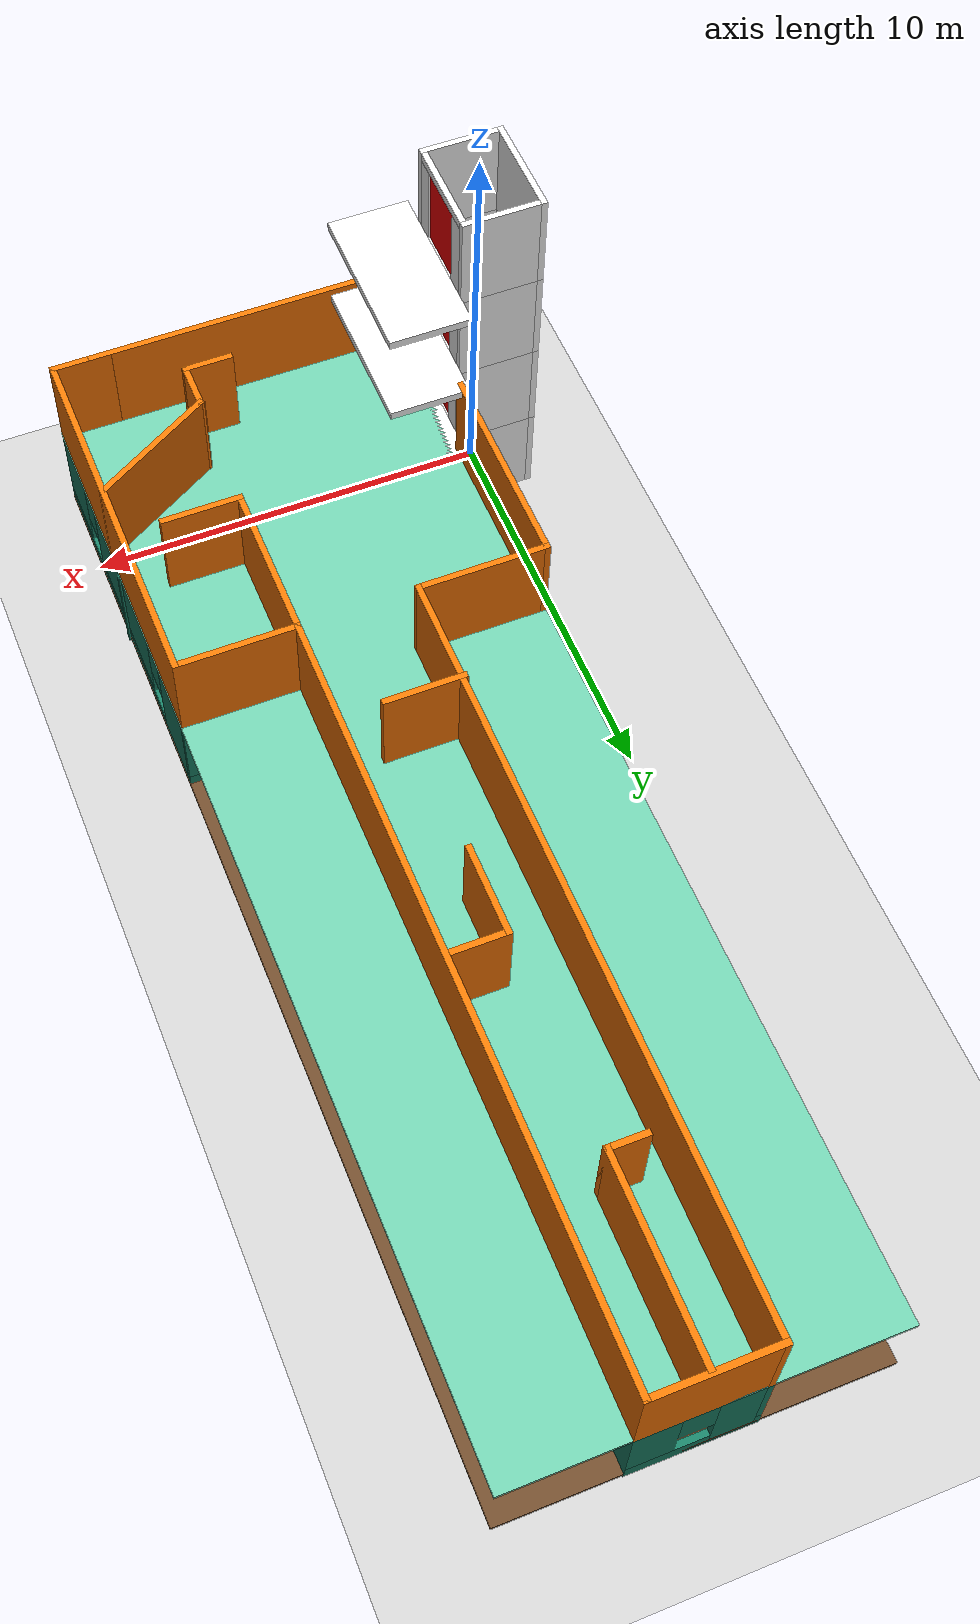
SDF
<?xml version='1.0' encoding='ASCII'?>
<sdf version='1.7'>
  <world name='tarkbot'>
    <physics type="ode">
      <max_step_size>0.003</max_step_size>
      <real_time_factor>1.0</real_time_factor>
    </physics>
    <plugin name='ignition::gazebo::systems::Physics' filename='libignition-gazebo-physics-system.so'/>
    <plugin name='ignition::gazebo::systems::UserCommands' filename='libignition-gazebo-user-commands-system.so'/>
    <plugin name='ignition::gazebo::systems::SceneBroadcaster' filename='libignition-gazebo-scene-broadcaster-system.so'/>

    <scene>
      <ambient>1 1 1 1</ambient>
      <background>0.3 0.7 0.9 1</background>
      <shadows>0</shadows>
      <grid>false</grid>
    </scene>

    <!-- TODO(rkreinin): Fix lighting so that spawning multiple robots does not crash the sim-->

    <model name="ground_plane">
      <static>true</static>
      <link name="link">
        <collision name="collision">
          <geometry>
            <plane>
              <normal>0 0 1</normal>
              <size>100 100</size>
            </plane>
          </geometry>
          <surface>
            <friction>
              <ode>
                <mu>50</mu>
              </ode>
            </friction>
          </surface>
        </collision>
        <visual name="visual">
          <geometry>
            <plane>
              <normal>0 0 1</normal>
              <size>100 100</size>
            </plane>
          </geometry>
          <material>
            <ambient>0.8 0.8 0.8 1</ambient>
            <diffuse>0.8 0.8 0.8 1</diffuse>
            <specular>0.8 0.8 0.8 1</specular>
          </material>
        </visual>
      </link>
    </model>

    <include>
      <uri>/home/fuzailx/ros2_ws/src/turtlebot4_simulator/turtlebot4_ignition_bringup/worlds/elevator.sdf</uri>
    </include>
    <include>
      <uri>/home/fuzailx/ros2_ws/src/turtlebot4_simulator/turtlebot4_ignition_bringup/worlds/building.sdf</uri>
    </include>

  </world>
</sdf>

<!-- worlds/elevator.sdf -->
<sdf version="1.6">
  <model name="elevator">
    <pose>0 0 0.2 0 0 0</pose>

    <!-- ========================= START OF WALLS ========================== -->
    <link name="structure">
      <kinematic>true</kinematic>
      <pose>0.0 0.0 0.0 0 0 0</pose>
      <inertial>
       <mass>1000</mass>
       <inertia>
         <ixx>8013.333333333336</ixx>
         <ixy>0</ixy>
         <ixz>0</ixz>
         <iyy>7893.333333333336</iyy>
         <iyz>0</iyz>
         <izz>546.6666666666667</izz>
       </inertia>
       <pose>0 0 2.4 0 0 0</pose>
     </inertial>

      <visual name="wall_front_bottom_visual_0">
        <pose>0.875 0.0 -0.1 0 0 0</pose>
        <geometry>
       <box>
         <size>0.15 2.3 0.2</size>
       </box>
     </geometry>
        <material>
          <ambient>1.0 1.0 1.0 1</ambient>
          <diffuse>1.0 1.0 1.0 1</diffuse>
          <specular>0.1 0.1 0.1 1</specular>
        </material>
      </visual>
      <collision name="wall_front_bottom_collision_0">
        <pose>0.875 0.0 -0.1 0 0 0</pose>
        <geometry>
       <box>
         <size>0.15 2.3 0.2</size>
       </box>
     </geometry>
      </collision>

      <visual name="wall_front_top_visual_0">
        <pose>0.875 0.0 2.1 0 0 0</pose>
        <geometry>
       <box>
         <size>0.15 2.3 0.2</size>
       </box>
     </geometry>
        <material>
          <ambient>1.0 1.0 1.0 1</ambient>
          <diffuse>1.0 1.0 1.0 1</diffuse>
          <specular>0.1 0.1 0.1 1</specular>
        </material>
      </visual>
      <collision name="wall_front_top_collision_0">
        <pose>0.875 0.0 2.1 0 0 0</pose>
        <geometry>
       <box>
         <size>0.15 2.3 0.2</size>
       </box>
     </geometry>
      </collision>

      <visual name="wall_front_right_visual_0">
        <pose>0.875 -0.925 1.0 0 0 0</pose>
        <geometry>
       <box>
         <size>0.15 0.45 2.0</size>
       </box>
     </geometry>
        <material>
          <ambient>1.0 1.0 1.0 1</ambient>
          <diffuse>1.0 1.0 1.0 1</diffuse>
          <specular>0.1 0.1 0.1 1</specular>
        </material>
      </visual>
      <collision name="wall_front_right_collision_0">
        <pose>0.875 -0.925 1.0 0 0 0</pose>
        <geometry>
       <box>
         <size>0.15 0.45 2.0</size>
       </box>
     </geometry>
      </collision>

      <visual name="wall_front_left_visual_0">
        <pose>0.875 0.925 1.0 0 0 0</pose>
        <geometry>
       <box>
         <size>0.15 0.45 2.0</size>
       </box>
     </geometry>
        <material>
          <ambient>1.0 1.0 1.0 1</ambient>
          <diffuse>1.0 1.0 1.0 1</diffuse>
          <specular>0.1 0.1 0.1 1</specular>
        </material>
      </visual>
      <collision name="wall_front_left_collision_0">
        <pose>0.875 0.925 1.0 0 0 0</pose>
        <geometry>
       <box>
         <size>0.15 0.45 2.0</size>
       </box>
     </geometry>
      </collision>

      <visual name="wall_right_visual_0">
        <pose>0.0 -1.225 1.0 0 0 0</pose>
        <geometry>
       <box>
         <size>1.9 0.15 2.4</size>
       </box>
     </geometry>
        <material>
          <ambient>1.0 1.0 1.0 1</ambient>
          <diffuse>1.0 1.0 1.0 1</diffuse>
          <specular>0.1 0.1 0.1 1</specular>
        </material>
      </visual>
      <collision name="wall_right_collision_0">
        <pose>0.0 -1.225 1.0 0 0 0</pose>
        <geometry>
       <box>
         <size>1.9 0.15 2.4</size>
       </box>
     </geometry>
      </collision>

      <visual name="wall_left_visual_0">
        <pose>0.0 1.225 1.0 0 0 0</pose>
        <geometry>
       <box>
         <size>1.9 0.15 2.4</size>
       </box>
     </geometry>
        <material>
          <ambient>1.0 1.0 1.0 1</ambient>
          <diffuse>1.0 1.0 1.0 1</diffuse>
          <specular>0.1 0.1 0.1 1</specular>
        </material>
      </visual>
      <collision name="wall_left_collision_0">
        <pose>0.0 1.225 1.0 0 0 0</pose>
        <geometry>
       <box>
         <size>1.9 0.15 2.4</size>
       </box>
     </geometry>
      </collision>

      <visual name="wall_rear_visual_0">
        <pose>-1.025 0.0 1.0 0 0 0</pose>
        <geometry>
       <box>
         <size>0.15 2.6 2.4</size>
       </box>
     </geometry>
        <material>
          <ambient>1.0 1.0 1.0 1</ambient>
          <diffuse>1.0 1.0 1.0 1</diffuse>
          <specular>0.1 0.1 0.1 1</specular>
        </material>
      </visual>
      <collision name="wall_rear_collision_0">
        <pose>-1.025 0.0 1.0 0 0 0</pose>
        <geometry>
       <box>
         <size>0.15 2.6 2.4</size>
       </box>
     </geometry>
      </collision>

      <visual name="entrance_visual_0">
        <pose>1.95 0.0 -0.1 0 0 0</pose>
        <geometry>
       <box>
         <size>2.0 4.0 0.2</size>
       </box>
     </geometry>
        <material>
          <ambient>1.0 1.0 1.0 1</ambient>
          <diffuse>1.0 1.0 1.0 1</diffuse>
          <specular>0.1 0.1 0.1 1</specular>
        </material>
      </visual>
      <collision name="entrance_collision_0">
        <pose>1.95 0.0 -0.1 0 0 0</pose>
        <geometry>
       <box>
         <size>2.0 4.0 0.2</size>
       </box>
     </geometry>
      </collision>

      <visual name="wall_front_bottom_visual_1">
        <pose>0.875 0.0 2.3 0 0 0</pose>
        <geometry>
       <box>
         <size>0.15 2.3 0.2</size>
       </box>
     </geometry>
        <material>
          <ambient>1.0 1.0 1.0 1</ambient>
          <diffuse>1.0 1.0 1.0 1</diffuse>
          <specular>0.1 0.1 0.1 1</specular>
        </material>
      </visual>
      <collision name="wall_front_bottom_collision_1">
        <pose>0.875 0.0 2.3 0 0 0</pose>
        <geometry>
       <box>
         <size>0.15 2.3 0.2</size>
       </box>
     </geometry>
      </collision>

      <visual name="wall_front_top_visual_1">
        <pose>0.875 0.0 4.5 0 0 0</pose>
        <geometry>
       <box>
         <size>0.15 2.3 0.2</size>
       </box>
     </geometry>
        <material>
          <ambient>1.0 1.0 1.0 1</ambient>
          <diffuse>1.0 1.0 1.0 1</diffuse>
          <specular>0.1 0.1 0.1 1</specular>
        </material>
      </visual>
      <collision name="wall_front_top_collision_1">
        <pose>0.875 0.0 4.5 0 0 0</pose>
        <geometry>
       <box>
         <size>0.15 2.3 0.2</size>
       </box>
     </geometry>
      </collision>

      <visual name="wall_front_right_visual_1">
        <pose>0.875 -0.925 3.4 0 0 0</pose>
        <geometry>
       <box>
         <size>0.15 0.45 2.0</size>
       </box>
     </geometry>
        <material>
          <ambient>1.0 1.0 1.0 1</ambient>
          <diffuse>1.0 1.0 1.0 1</diffuse>
          <specular>0.1 0.1 0.1 1</specular>
        </material>
      </visual>
      <collision name="wall_front_right_collision_1">
        <pose>0.875 -0.925 3.4 0 0 0</pose>
        <geometry>
       <box>
         <size>0.15 0.45 2.0</size>
       </box>
     </geometry>
      </collision>

      <visual name="wall_front_left_visual_1">
        <pose>0.875 0.925 3.4 0 0 0</pose>
        <geometry>
       <box>
         <size>0.15 0.45 2.0</size>
       </box>
     </geometry>
        <material>
          <ambient>1.0 1.0 1.0 1</ambient>
          <diffuse>1.0 1.0 1.0 1</diffuse>
          <specular>0.1 0.1 0.1 1</specular>
        </material>
      </visual>
      <collision name="wall_front_left_collision_1">
        <pose>0.875 0.925 3.4 0 0 0</pose>
        <geometry>
       <box>
         <size>0.15 0.45 2.0</size>
       </box>
     </geometry>
      </collision>

      <visual name="wall_right_visual_1">
        <pose>0.0 -1.225 3.4 0 0 0</pose>
        <geometry>
       <box>
         <size>1.9 0.15 2.4</size>
       </box>
     </geometry>
        <material>
          <ambient>1.0 1.0 1.0 1</ambient>
          <diffuse>1.0 1.0 1.0 1</diffuse>
          <specular>0.1 0.1 0.1 1</specular>
        </material>
      </visual>
      <collision name="wall_right_collision_1">
        <pose>0.0 -1.225 3.4 0 0 0</pose>
        <geometry>
       <box>
         <size>1.9 0.15 2.4</size>
       </box>
     </geometry>
      </collision>

      <visual name="wall_left_visual_1">
        <pose>0.0 1.225 3.4 0 0 0</pose>
        <geometry>
       <box>
         <size>1.9 0.15 2.4</size>
       </box>
     </geometry>
        <material>
          <ambient>1.0 1.0 1.0 1</ambient>
          <diffuse>1.0 1.0 1.0 1</diffuse>
          <specular>0.1 0.1 0.1 1</specular>
        </material>
      </visual>
      <collision name="wall_left_collision_1">
        <pose>0.0 1.225 3.4 0 0 0</pose>
        <geometry>
       <box>
         <size>1.9 0.15 2.4</size>
       </box>
     </geometry>
      </collision>

      <visual name="wall_rear_visual_1">
        <pose>-1.025 0.0 3.4 0 0 0</pose>
        <geometry>
       <box>
         <size>0.15 2.6 2.4</size>
       </box>
     </geometry>
        <material>
          <ambient>1.0 1.0 1.0 1</ambient>
          <diffuse>1.0 1.0 1.0 1</diffuse>
          <specular>0.1 0.1 0.1 1</specular>
        </material>
      </visual>
      <collision name="wall_rear_collision_1">
        <pose>-1.025 0.0 3.4 0 0 0</pose>
        <geometry>
       <box>
         <size>0.15 2.6 2.4</size>
       </box>
     </geometry>
      </collision>

      <visual name="entrance_visual_1">
        <pose>1.95 0.0 2.3 0 0 0</pose>
        <geometry>
       <box>
         <size>2.0 4.0 0.2</size>
       </box>
     </geometry>
        <material>
          <ambient>1.0 1.0 1.0 1</ambient>
          <diffuse>1.0 1.0 1.0 1</diffuse>
          <specular>0.1 0.1 0.1 1</specular>
        </material>
      </visual>
      <collision name="entrance_collision_1">
        <pose>1.95 0.0 2.3 0 0 0</pose>
        <geometry>
       <box>
         <size>2.0 4.0 0.2</size>
       </box>
     </geometry>
      </collision>

      <visual name="wall_front_bottom_visual_2">
        <pose>0.875 0.0 4.7 0 0 0</pose>
        <geometry>
       <box>
         <size>0.15 2.3 0.2</size>
       </box>
     </geometry>
        <material>
          <ambient>1.0 1.0 1.0 1</ambient>
          <diffuse>1.0 1.0 1.0 1</diffuse>
          <specular>0.1 0.1 0.1 1</specular>
        </material>
      </visual>
      <collision name="wall_front_bottom_collision_2">
        <pose>0.875 0.0 4.7 0 0 0</pose>
        <geometry>
       <box>
         <size>0.15 2.3 0.2</size>
       </box>
     </geometry>
      </collision>

      <visual name="wall_front_top_visual_2">
        <pose>0.875 0.0 6.9 0 0 0</pose>
        <geometry>
       <box>
         <size>0.15 2.3 0.2</size>
       </box>
     </geometry>
        <material>
          <ambient>1.0 1.0 1.0 1</ambient>
          <diffuse>1.0 1.0 1.0 1</diffuse>
          <specular>0.1 0.1 0.1 1</specular>
        </material>
      </visual>
      <collision name="wall_front_top_collision_2">
        <pose>0.875 0.0 6.9 0 0 0</pose>
        <geometry>
       <box>
         <size>0.15 2.3 0.2</size>
       </box>
     </geometry>
      </collision>

      <visual name="wall_front_right_visual_2">
        <pose>0.875 -0.925 5.8 0 0 0</pose>
        <geometry>
       <box>
         <size>0.15 0.45 2.0</size>
       </box>
     </geometry>
        <material>
          <ambient>1.0 1.0 1.0 1</ambient>
          <diffuse>1.0 1.0 1.0 1</diffuse>
          <specular>0.1 0.1 0.1 1</specular>
        </material>
      </visual>
      <collision name="wall_front_right_collision_2">
        <pose>0.875 -0.925 5.8 0 0 0</pose>
        <geometry>
       <box>
         <size>0.15 0.45 2.0</size>
       </box>
     </geometry>
      </collision>

      <visual name="wall_front_left_visual_2">
        <pose>0.875 0.925 5.8 0 0 0</pose>
        <geometry>
       <box>
         <size>0.15 0.45 2.0</size>
       </box>
     </geometry>
        <material>
          <ambient>1.0 1.0 1.0 1</ambient>
          <diffuse>1.0 1.0 1.0 1</diffuse>
          <specular>0.1 0.1 0.1 1</specular>
        </material>
      </visual>
      <collision name="wall_front_left_collision_2">
        <pose>0.875 0.925 5.8 0 0 0</pose>
        <geometry>
       <box>
         <size>0.15 0.45 2.0</size>
       </box>
     </geometry>
      </collision>

      <visual name="wall_right_visual_2">
        <pose>0.0 -1.225 5.8 0 0 0</pose>
        <geometry>
       <box>
         <size>1.9 0.15 2.4</size>
       </box>
     </geometry>
        <material>
          <ambient>1.0 1.0 1.0 1</ambient>
          <diffuse>1.0 1.0 1.0 1</diffuse>
          <specular>0.1 0.1 0.1 1</specular>
        </material>
      </visual>
      <collision name="wall_right_collision_2">
        <pose>0.0 -1.225 5.8 0 0 0</pose>
        <geometry>
       <box>
         <size>1.9 0.15 2.4</size>
       </box>
     </geometry>
      </collision>

      <visual name="wall_left_visual_2">
        <pose>0.0 1.225 5.8 0 0 0</pose>
        <geometry>
       <box>
         <size>1.9 0.15 2.4</size>
       </box>
     </geometry>
        <material>
          <ambient>1.0 1.0 1.0 1</ambient>
          <diffuse>1.0 1.0 1.0 1</diffuse>
          <specular>0.1 0.1 0.1 1</specular>
        </material>
      </visual>
      <collision name="wall_left_collision_2">
        <pose>0.0 1.225 5.8 0 0 0</pose>
        <geometry>
       <box>
         <size>1.9 0.15 2.4</size>
       </box>
     </geometry>
      </collision>

      <visual name="wall_rear_visual_2">
        <pose>-1.025 0.0 5.8 0 0 0</pose>
        <geometry>
       <box>
         <size>0.15 2.6 2.4</size>
       </box>
     </geometry>
        <material>
          <ambient>1.0 1.0 1.0 1</ambient>
          <diffuse>1.0 1.0 1.0 1</diffuse>
          <specular>0.1 0.1 0.1 1</specular>
        </material>
      </visual>
      <collision name="wall_rear_collision_2">
        <pose>-1.025 0.0 5.8 0 0 0</pose>
        <geometry>
       <box>
         <size>0.15 2.6 2.4</size>
       </box>
     </geometry>
      </collision>

      <visual name="entrance_visual_2">
        <pose>1.95 0.0 4.7 0 0 0</pose>
        <geometry>
       <box>
         <size>2.0 4.0 0.2</size>
       </box>
     </geometry>
        <material>
          <ambient>1.0 1.0 1.0 1</ambient>
          <diffuse>1.0 1.0 1.0 1</diffuse>
          <specular>0.1 0.1 0.1 1</specular>
        </material>
      </visual>
      <collision name="entrance_collision_2">
        <pose>1.95 0.0 4.7 0 0 0</pose>
        <geometry>
       <box>
         <size>2.0 4.0 0.2</size>
       </box>
     </geometry>
      </collision>

      <visual name="wall_front_bottom_visual_3">
        <pose>0.875 0.0 7.1 0 0 0</pose>
        <geometry>
       <box>
         <size>0.15 2.3 0.2</size>
       </box>
     </geometry>
        <material>
          <ambient>1.0 1.0 1.0 1</ambient>
          <diffuse>1.0 1.0 1.0 1</diffuse>
          <specular>0.1 0.1 0.1 1</specular>
        </material>
      </visual>
      <collision name="wall_front_bottom_collision_3">
        <pose>0.875 0.0 7.1 0 0 0</pose>
        <geometry>
       <box>
         <size>0.15 2.3 0.2</size>
       </box>
     </geometry>
      </collision>

      <visual name="wall_front_top_visual_3">
        <pose>0.875 0.0 9.3 0 0 0</pose>
        <geometry>
       <box>
         <size>0.15 2.3 0.2</size>
       </box>
     </geometry>
        <material>
          <ambient>1.0 1.0 1.0 1</ambient>
          <diffuse>1.0 1.0 1.0 1</diffuse>
          <specular>0.1 0.1 0.1 1</specular>
        </material>
      </visual>
      <collision name="wall_front_top_collision_3">
        <pose>0.875 0.0 9.3 0 0 0</pose>
        <geometry>
       <box>
         <size>0.15 2.3 0.2</size>
       </box>
     </geometry>
      </collision>

      <visual name="wall_front_right_visual_3">
        <pose>0.875 -0.925 8.2 0 0 0</pose>
        <geometry>
       <box>
         <size>0.15 0.45 2.0</size>
       </box>
     </geometry>
        <material>
          <ambient>1.0 1.0 1.0 1</ambient>
          <diffuse>1.0 1.0 1.0 1</diffuse>
          <specular>0.1 0.1 0.1 1</specular>
        </material>
      </visual>
      <collision name="wall_front_right_collision_3">
        <pose>0.875 -0.925 8.2 0 0 0</pose>
        <geometry>
       <box>
         <size>0.15 0.45 2.0</size>
       </box>
     </geometry>
      </collision>

      <visual name="wall_front_left_visual_3">
        <pose>0.875 0.925 8.2 0 0 0</pose>
        <geometry>
       <box>
         <size>0.15 0.45 2.0</size>
       </box>
     </geometry>
        <material>
          <ambient>1.0 1.0 1.0 1</ambient>
          <diffuse>1.0 1.0 1.0 1</diffuse>
          <specular>0.1 0.1 0.1 1</specular>
        </material>
      </visual>
      <collision name="wall_front_left_collision_3">
        <pose>0.875 0.925 8.2 0 0 0</pose>
        <geometry>
       <box>
         <size>0.15 0.45 2.0</size>
       </box>
     </geometry>
      </collision>

      <visual name="wall_right_visual_3">
        <pose>0.0 -1.225 8.2 0 0 0</pose>
        <geometry>
       <box>
         <size>1.9 0.15 2.4</size>
       </box>
     </geometry>
        <material>
          <ambient>1.0 1.0 1.0 1</ambient>
          <diffuse>1.0 1.0 1.0 1</diffuse>
          <specular>0.1 0.1 0.1 1</specular>
        </material>
      </visual>
      <collision name="wall_right_collision_3">
        <pose>0.0 -1.225 8.2 0 0 0</pose>
        <geometry>
       <box>
         <size>1.9 0.15 2.4</size>
       </box>
     </geometry>
      </collision>

      <visual name="wall_left_visual_3">
        <pose>0.0 1.225 8.2 0 0 0</pose>
        <geometry>
       <box>
         <size>1.9 0.15 2.4</size>
       </box>
     </geometry>
        <material>
          <ambient>1.0 1.0 1.0 1</ambient>
          <diffuse>1.0 1.0 1.0 1</diffuse>
          <specular>0.1 0.1 0.1 1</specular>
        </material>
      </visual>
      <collision name="wall_left_collision_3">
        <pose>0.0 1.225 8.2 0 0 0</pose>
        <geometry>
       <box>
         <size>1.9 0.15 2.4</size>
       </box>
     </geometry>
      </collision>

      <visual name="wall_rear_visual_3">
        <pose>-1.025 0.0 8.2 0 0 0</pose>
        <geometry>
       <box>
         <size>0.15 2.6 2.4</size>
       </box>
     </geometry>
        <material>
          <ambient>1.0 1.0 1.0 1</ambient>
          <diffuse>1.0 1.0 1.0 1</diffuse>
          <specular>0.1 0.1 0.1 1</specular>
        </material>
      </visual>
      <collision name="wall_rear_collision_3">
        <pose>-1.025 0.0 8.2 0 0 0</pose>
        <geometry>
       <box>
         <size>0.15 2.6 2.4</size>
       </box>
     </geometry>
      </collision>

      <visual name="entrance_visual_3">
        <pose>1.95 0.0 7.1 0 0 0</pose>
        <geometry>
       <box>
         <size>2.0 4.0 0.2</size>
       </box>
     </geometry>
        <material>
          <ambient>1.0 1.0 1.0 1</ambient>
          <diffuse>1.0 1.0 1.0 1</diffuse>
          <specular>0.1 0.1 0.1 1</specular>
        </material>
      </visual>
      <collision name="entrance_collision_3">
        <pose>1.95 0.0 7.1 0 0 0</pose>
        <geometry>
       <box>
         <size>2.0 4.0 0.2</size>
       </box>
     </geometry>
      </collision>

    </link>
    <joint name="foundation" type="fixed">
      <parent>world</parent>
      <child>structure</child>
    </joint>
    <!-- ========================== END OF WALLS =========================== -->

    <!-- ========================= START OF DOORS ========================== -->

    <link name="door_panel_0">
      <pose>0.85 0.0 1.0 0 0 0</pose>
      <inertial>
       <mass>20</mass>
       <inertia>
         <ixx>9.933333333333334</ixx>
         <ixy>0</ixy>
         <ixz>0</ixz>
         <iyy>6.683333333333333</iyy>
         <iyz>0</iyz>
         <izz>3.2833333333333328</izz>
       </inertia>
       <pose>0 0 0 0 0 0</pose>
     </inertial>
      <visual name="door_visual_0">
        <geometry>
       <box>
         <size>0.1 1.4 2.0</size>
       </box>
     </geometry>
        <material>
          <ambient>1.0 0.0 0.0 1</ambient>
          <diffuse>1.0 0.0 0.0 1</diffuse>
          <specular>0.1 0.1 0.1 1</specular>
        </material>
      </visual>
      <collision name="door_collision_0">
        <geometry>
       <box>
         <size>0.1 1.4 2.0</size>
       </box>
     </geometry>
      </collision>
    </link>
    <joint name="door_0" type="prismatic">
      <parent>structure</parent>
      <child>door_panel_0</child>
      <axis>
        <xyz>0 1 0</xyz>
        <limit>
          <lower>0</lower>
          <upper>1.4</upper>
          <effort>5000</effort>
          <velocity>0.3</velocity>
        </limit>
        <dynamics>
          <damping>30</damping>
        </dynamics>
      </axis>
    </joint>
    <plugin
      filename="ignition-gazebo-joint-position-controller-system"
      name="ignition::gazebo::systems::JointPositionController">
      <joint_name>door_0</joint_name>
      <p_gain>60</p_gain>
      <i_gain>0</i_gain>
      <d_gain>40</d_gain>
      <cmd_min>-20</cmd_min>
      <cmd_max>20</cmd_max>
    </plugin>

    <link name="door_panel_1">
      <pose>0.85 0.0 3.4 0 0 0</pose>
      <inertial>
       <mass>20</mass>
       <inertia>
         <ixx>9.933333333333334</ixx>
         <ixy>0</ixy>
         <ixz>0</ixz>
         <iyy>6.683333333333333</iyy>
         <iyz>0</iyz>
         <izz>3.2833333333333328</izz>
       </inertia>
       <pose>0 0 0 0 0 0</pose>
     </inertial>
      <visual name="door_visual_1">
        <geometry>
       <box>
         <size>0.1 1.4 2.0</size>
       </box>
     </geometry>
        <material>
          <ambient>1.0 0.0 0.0 1</ambient>
          <diffuse>1.0 0.0 0.0 1</diffuse>
          <specular>0.1 0.1 0.1 1</specular>
        </material>
      </visual>
      <collision name="door_collision_1">
        <geometry>
       <box>
         <size>0.1 1.4 2.0</size>
       </box>
     </geometry>
      </collision>
    </link>
    <joint name="door_1" type="prismatic">
      <parent>structure</parent>
      <child>door_panel_1</child>
      <axis>
        <xyz>0 1 0</xyz>
        <limit>
          <lower>0</lower>
          <upper>1.4</upper>
          <effort>5000</effort>
          <velocity>0.3</velocity>
        </limit>
        <dynamics>
          <damping>30</damping>
        </dynamics>
      </axis>
    </joint>
    <plugin
      filename="ignition-gazebo-joint-position-controller-system"
      name="ignition::gazebo::systems::JointPositionController">
      <joint_name>door_1</joint_name>
      <p_gain>60</p_gain>
      <i_gain>0</i_gain>
      <d_gain>40</d_gain>
      <cmd_min>-20</cmd_min>
      <cmd_max>20</cmd_max>
    </plugin>

    <link name="door_panel_2">
      <pose>0.85 0.0 5.8 0 0 0</pose>
      <inertial>
       <mass>20</mass>
       <inertia>
         <ixx>9.933333333333334</ixx>
         <ixy>0</ixy>
         <ixz>0</ixz>
         <iyy>6.683333333333333</iyy>
         <iyz>0</iyz>
         <izz>3.2833333333333328</izz>
       </inertia>
       <pose>0 0 0 0 0 0</pose>
     </inertial>
      <visual name="door_visual_2">
        <geometry>
       <box>
         <size>0.1 1.4 2.0</size>
       </box>
     </geometry>
        <material>
          <ambient>1.0 0.0 0.0 1</ambient>
          <diffuse>1.0 0.0 0.0 1</diffuse>
          <specular>0.1 0.1 0.1 1</specular>
        </material>
      </visual>
      <collision name="door_collision_2">
        <geometry>
       <box>
         <size>0.1 1.4 2.0</size>
       </box>
     </geometry>
      </collision>
    </link>
    <joint name="door_2" type="prismatic">
      <parent>structure</parent>
      <child>door_panel_2</child>
      <axis>
        <xyz>0 1 0</xyz>
        <limit>
          <lower>0</lower>
          <upper>1.4</upper>
          <effort>5000</effort>
          <velocity>0.1</velocity>
        </limit>
        <dynamics>
          <damping>30</damping>
        </dynamics>
      </axis>
    </joint>
    <plugin
      filename="ignition-gazebo-joint-position-controller-system"
      name="ignition::gazebo::systems::JointPositionController">
      <joint_name>door_2</joint_name>
      <p_gain>60</p_gain>
      <i_gain>0</i_gain>
      <d_gain>40</d_gain>
      <cmd_min>-20</cmd_min>
      <cmd_max>20</cmd_max>
    </plugin>

    <link name="door_panel_3">
      <pose>0.85 0.0 8.2 0 0 0</pose>
      <inertial>
       <mass>20</mass>
       <inertia>
         <ixx>9.933333333333334</ixx>
         <ixy>0</ixy>
         <ixz>0</ixz>
         <iyy>6.683333333333333</iyy>
         <iyz>0</iyz>
         <izz>3.2833333333333328</izz>
       </inertia>
       <pose>0 0 0 0 0 0</pose>
     </inertial>
      <visual name="door_visual_3">
        <geometry>
       <box>
         <size>0.1 1.4 2.0</size>
       </box>
     </geometry>
        <material>
          <ambient>1.0 0.0 0.0 1</ambient>
          <diffuse>1.0 0.0 0.0 1</diffuse>
          <specular>0.1 0.1 0.1 1</specular>
        </material>
      </visual>
      <collision name="door_collision_3">
        <geometry>
       <box>
         <size>0.1 1.4 2.0</size>
       </box>
     </geometry>
      </collision>
    </link>
    <joint name="door_3" type="prismatic">
      <parent>structure</parent>
      <child>door_panel_3</child>
      <axis>
        <xyz>0 1 0</xyz>
        <limit>
          <lower>0</lower>
          <upper>1.4</upper>
          <effort>5000</effort>
          <velocity>0.1</velocity>
        </limit>
        <dynamics>
          <damping>30</damping>
        </dynamics>
      </axis>
    </joint>
    <plugin
      filename="ignition-gazebo-joint-position-controller-system"
      name="ignition::gazebo::systems::JointPositionController">
      <joint_name>door_3</joint_name>
      <p_gain>60</p_gain>
      <i_gain>0</i_gain>
      <d_gain>40</d_gain>
      <cmd_min>-20</cmd_min>
      <cmd_max>20</cmd_max>
    </plugin>

    <!-- ========================== END OF DOORS =========================== -->

    <!-- ========================= START OF CABIN ========================== -->
    <link name="cabin">
      <pose>0.0 0.0 0.0 0 0 0</pose>
      <inertial>
       <mass>200</mass>
       <inertia>
         <ixx>147.33333333333334</ixx>
         <ixy>0</ixy>
         <ixz>0</ixz>
         <iyy>123.33333333333336</iyy>
         <iyz>0</iyz>
         <izz>109.33333333333333</izz>
       </inertia>
       <pose>0 0 1.1 0 0 0</pose>
     </inertial>

      <light type="spot" name="spot_0">
        <pose>0 -0.5 2.09 0 0 0</pose>
        <diffuse>1 1 1 1</diffuse>
        <specular>.2 .2 .2 1</specular>
        <attenuation>
          <range>2.2</range>
          <linear>0.2</linear>
          <constant>0.05</constant>
          <quadratic>0.01</quadratic>
        </attenuation>
        <direction>0 0 1</direction>
        <spot>
          <inner_angle>0.1</inner_angle>
          <outer_angle>1.0</outer_angle>
          <falloff>0.8</falloff>
        </spot>
        <cast_shadows>true</cast_shadows>
      </light>

      <light type="spot" name="spot_1">
        <pose>0 0.5 2.09 0 0 0</pose>
        <diffuse>1 1 1 1</diffuse>
        <specular>.2 .2 .2 1</specular>
        <attenuation>
          <range>2.2</range>
          <linear>0.2</linear>
          <constant>0.05</constant>
          <quadratic>0.01</quadratic>
        </attenuation>
        <direction>0 0 1</direction>
        <spot>
          <inner_angle>0.1</inner_angle>
          <outer_angle>1.0</outer_angle>
          <falloff>0.8</falloff>
        </spot>
        <cast_shadows>true</cast_shadows>
      </light>

      <visual name="cabin_bottom_visual">
        <pose>0 0 -0.05 0 0 0</pose>
        <geometry>
       <box>
         <size>1.6 2.0 0.1</size>5
       </box>
     </geometry>
        <material>
          <ambient>0.175 0.175 0.175 1</ambient>
          <diffuse>0.175 0.175 0.175 1</diffuse>
          <specular>0.1 0.1 0.1 1</specular>
        </material>
      </visual>
      <collision name="cabin_bottom_collision">
        <pose>0 0 -0.05 0 0 0</pose>
        <geometry>
       <box>
         <size>1.6 2.0 0.1</size>
       </box>
     </geometry>
      </collision>

      <visual name="cabin_top_visual">
        <pose>0 0 2.25 0 0 0</pose>
        <geometry>
       <box>
         <size>1.6 2.0 0.1</size>
       </box>
     </geometry>
        <material>
          <ambient>0.175 0.175 0.175 1</ambient>
          <diffuse>0.175 0.175 0.175 1</diffuse>
          <specular>0.1 0.1 0.1 1</specular>
        </material>
      </visual>
      <collision name="cabin_top_collision">
        <pose>0 0 2.25 0 0 0</pose>
        <geometry>
       <box>
         <size>1.6 2.0 0.1</size>
       </box>
     </geometry>
      </collision>

      <visual name="cabin_right_visual">
        <pose>0 -1.05 1.1 0 0 0</pose>
        <geometry>
       <box>
         <size>1.6 0.1 2.4</size>
       </box>
     </geometry>
        <material>
          <ambient>0.175 0.175 0.175 1</ambient>
          <diffuse>0.175 0.175 0.175 1</diffuse>
          <specular>0.1 0.1 0.1 1</specular>
        </material>
      </visual>
      <collision name="cabin_right_collision">
        <pose>0 -1.05 1.1 0 0 0</pose>
        <geometry>
       <box>
         <size>1.6 0.1 2.4</size>
       </box>
     </geometry>
      </collision>

      <visual name="cabin_left_visual">
        <pose>0 1.05 1.1 0 0 0</pose>
        <geometry>
       <box>
         <size>1.6 0.1 2.4</size>
       </box>
     </geometry>
        <material>
          <ambient>0.175 0.175 0.175 1</ambient>
          <diffuse>0.175 0.175 0.175 1</diffuse>
          <specular>0.1 0.1 0.1 1</specular>
        </material>
      </visual>
      <collision name="cabin_left_collision">
        <pose>0 1.05 1.1 0 0 0</pose>
        <geometry>
       <box>
         <size>1.6 0.1 2.4</size>
       </box>
     </geometry>
      </collision>

      <visual name="cabin_rear_visual">
        <pose>-0.85 0 1.1 0 0 0</pose>
        <geometry>
       <box>
         <size>0.1 2.2 2.4</size>
       </box>
     </geometry>
        <material>
          <ambient>0.175 0.175 0.175 1</ambient>
          <diffuse>0.175 0.175 0.175 1</diffuse>
          <specular>0.1 0.1 0.1 1</specular>
        </material>
      </visual>
      <collision name="cabin_rear_collision">
        <pose>-0.85 0 1.1 0 0 0</pose>
        <geometry>
       <box>
         <size>0.1 2.2 2.4</size>
       </box>
     </geometry>
      </collision>

    </link>
    <joint name="lift" type="prismatic">
      <parent>structure</parent>
      <child>cabin</child>
      <axis>
        <xyz>0 0 1</xyz>
        <limit>
          <lower>0</lower>
          <upper>7.200000000000001</upper>
          <effort>50000000</effort>
          <velocity>0.5</velocity>
        </limit>
        <dynamics>
          <damping>180000</damping>
        </dynamics>
      </axis>
    </joint>
    <plugin
      filename="ignition-gazebo-joint-position-controller-system"
      name="ignition::gazebo::systems::JointPositionController">
      <joint_name>lift</joint_name>
      <p_gain>4000000</p_gain>
      <i_gain>2000</i_gain>
      <d_gain>5000</d_gain>
      <i_min>-2000</i_min>
      <i_max>2000</i_max>
      <cmd_min>-80000</cmd_min>
      <cmd_max>120000</cmd_max>
    </plugin>
    <!-- ========================== END OF CABIN =========================== -->

    <!-- =================== START OF FLOOR REFERENCES ===================== -->

    <link name="floor_0">
      <pose>0.0 0.0 0.0 0 0 0</pose>
    </link>
    <joint name="floor_0_joint" type="fixed">
      <parent>structure</parent>
      <child>floor_0</child>
    </joint>

    <link name="floor_1">
      <pose>0.0 0.0 2.4 0 0 0</pose>
    </link>
    <joint name="floor_1_joint" type="fixed">
      <parent>structure</parent>
      <child>floor_1</child>
    </joint>

    <link name="floor_2">
      <pose>0.0 0.0 4.8 0 0 0</pose>
    </link>
    <joint name="floor_2_joint" type="fixed">
      <parent>structure</parent>
      <child>floor_2</child>
    </joint>

    <link name="floor_3">
      <pose>0.0 0.0 7.2 0 0 0</pose>
    </link>
    <joint name="floor_3_joint" type="fixed">
      <parent>structure</parent>
      <child>floor_3</child>
    </joint>

    <!-- ==================== END OF FLOOR REFERENCES ====================== -->

    <!-- ===================== START OF DOOR LIDARS ======================== -->

    <link name="door_lidar_0">
      <pose>0.875 -0.7 0.2 1.5707963267948966 0 1.5707963267948966</pose>
      <sensor name="sensor" type="gpu_lidar">
        <topic>model/elevator/door_0/lidar</topic>
        <update_rate>10</update_rate>
        <lidar>
          <scan>
            <horizontal>
              <samples>1</samples>
              <resolution>1</resolution>
              <min_angle>0</min_angle>
              <max_angle>0</max_angle>
            </horizontal>
          </scan>
          <range>
            <min>0.001</min>
            <max>1.395</max>
            <resolution>0.01</resolution>
          </range>
        </lidar>
      </sensor>
    </link>
    <joint name="door_lidar_0_joint" type="fixed">
      <parent>structure</parent>
      <child>door_lidar_0</child>
    </joint>

    <link name="door_lidar_1">
      <pose>0.875 -0.7 2.6 1.5707963267948966 0 1.5707963267948966</pose>
      <sensor name="sensor" type="gpu_lidar">
        <topic>model/elevator/door_1/lidar</topic>
        <update_rate>10</update_rate>
        <lidar>
          <scan>
            <horizontal>
              <samples>1</samples>
              <resolution>1</resolution>
              <min_angle>0</min_angle>
              <max_angle>0</max_angle>
            </horizontal>
          </scan>
          <range>
            <min>0.001</min>
            <max>1.395</max>
            <resolution>0.01</resolution>
          </range>
        </lidar>
      </sensor>
    </link>
    <joint name="door_lidar_1_joint" type="fixed">
      <parent>structure</parent>
      <child>door_lidar_1</child>
    </joint>

    <link name="door_lidar_2">
      <pose>0.875 -0.7 5.0 1.5707963267948966 0 1.5707963267948966</pose>
      <sensor name="sensor" type="gpu_lidar">
        <topic>model/elevator/door_2/lidar</topic>
        <update_rate>10</update_rate>
        <lidar>
          <scan>
            <horizontal>
              <samples>1</samples>
              <resolution>1</resolution>
              <min_angle>0</min_angle>
              <max_angle>0</max_angle>
            </horizontal>
          </scan>
          <range>
            <min>0.001</min>
            <max>1.395</max>
            <resolution>0.01</resolution>
          </range>
        </lidar>
      </sensor>
    </link>
    <joint name="door_lidar_2_joint" type="fixed">
      <parent>structure</parent>
      <child>door_lidar_2</child>
    </joint>

    <link name="door_lidar_3">
      <pose>0.875 -0.7 7.4 1.5707963267948966 0 1.5707963267948966</pose>
      <sensor name="sensor" type="gpu_lidar">
        <topic>model/elevator/door_3/lidar</topic>
        <update_rate>10</update_rate>
        <lidar>
          <scan>
            <horizontal>
              <samples>1</samples>
              <resolution>1</resolution>
              <min_angle>0</min_angle>
              <max_angle>0</max_angle>
            </horizontal>
          </scan>
          <range>
            <min>0.001</min>
            <max>1.395</max>
            <resolution>0.01</resolution>
          </range>
        </lidar>
      </sensor>
    </link>
    <joint name="door_lidar_3_joint" type="fixed">
      <parent>structure</parent>
      <child>door_lidar_3</child>
    </joint>

    <!-- ====================== END OF DOOR LIDARS ========================= -->

    <!-- ====================== START OF CONTROLLER ======================== -->
    <plugin
      filename="ignition-gazebo-elevator-system"
      name="ignition::gazebo::systems::Elevator">
    </plugin>
    <!-- ======================= END OF CONTROLLER ========================= -->

  </model>
</sdf>

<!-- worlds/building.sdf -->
<sdf version='1.7'>
  <model name='mulyi_floor_v2'>
    <pose>5.5 11.5 0 0 -0 -1.57</pose>
    <link name='Floor_2'>
      <collision name='Floor_2_Collision'>
        <geometry>
          <box>
            <size>27.6 8.96003 0.1</size>
          </box>
        </geometry>
        <pose>0 0 0.05 0 -0 0</pose>
      </collision>
      <visual name='Floor_2_Visual'>
        <pose>0 0 0.05 0 -0 0</pose>
        <geometry>
          <box>
            <size>27.6 8.96003 0.1</size>
          </box>
        </geometry>
        <material>
          <diffuse>0.435294 0.796078 0.67451 1</diffuse>
            <specular>0.435294 0.796078 0.67451 1</specular>
          <ambient>0.435294 0.796078 0.67451 1</ambient>
        </material>
        <meta>
          <layer>1</layer>
        </meta>
      </visual>
      <pose>0 -0.019886 2.5 0 -0 0</pose>
    </link>
    <link name='Floor_1'>
      <collision name='Floor_1_Collision'>
        <geometry>
          <box>
            <size>50.6 8.96003 0.1</size>
          </box>
        </geometry>
        <pose>0 0 0.05 0 -0 0</pose>
      </collision>
      <visual name='Floor_1_Visual'>
        <pose>0 0 0.05 0 -0 0</pose>
        <geometry>
          <box>
            <size>27.6 8.96003 0.1</size>
          </box>
        </geometry>
        <material>
          <diffuse>0.435294 0.296078 0.17451 1</diffuse>
            <specular>0.435294 0.296078 0.17451 1</specular>
          <ambient>0.435294 0.296078 0.17451 1</ambient>
        </material>
        <meta>
          <layer>0</layer>
        </meta>
      </visual>
      <pose>0 -0.019886 0.1 0 -0 0</pose>
    </link>
    <link name='Wall_101'>
      <collision name='Wall_101_Collision'>
        <geometry>
          <box>
            <size>5.25 0.15 2.5</size>
          </box>
        </geometry>
        <pose>0 0 1.25 0 -0 0</pose>
      </collision>
      <visual name='Wall_101_Visual'>
        <pose>0 0 1.25 0 -0 0</pose>
        <geometry>
          <box>
            <size>5.25 0.15 2.5</size>
          </box>
        </geometry>
        <material>
          <diffuse>0.098039 0.501960 0.400000 0.9</diffuse>
            <specular>0.098039 0.501960 0.400000 0.9</specular>
          <ambient>0.098039 0.501960 0.400000 0.9</ambient>
        </material>
        <meta>
          <layer>0</layer>
        </meta>
      </visual>
      <pose>7.175 -4.4249 0 0 -0 0</pose>
    </link>
    <link name='Wall_103'>
      <collision name='Wall_103_Collision'>
        <geometry>
          <box>
            <size>8 0.15 2.5</size>
          </box>
        </geometry>
        <pose>0 0 1.25 0 -0 0</pose>
      </collision>
      <visual name='Wall_103_Visual'>
        <pose>0 0 1.25 0 -0 0</pose>
        <geometry>
          <box>
            <size>8 0.15 2.5</size>
          </box>
        </geometry>
        <material>
          <diffuse>0.996078 0.47451 0.0196078 1</diffuse>
            <specular>0.996078 0.47451 0.0196078 1</specular>
          <ambient>0.996078 0.47451 0.0196078 1</ambient>
        </material>
        <meta>
          <layer>1</layer>
        </meta>
      </visual>
      <pose>13.725 -0.499902 2.5 0 -0 -1.5708</pose>
    </link>
    <link name='Wall_104'>
      <collision name='Wall_104_Collision'>
        <geometry>
          <box>
            <size>3.25 0.15 2.5</size>
          </box>
        </geometry>
        <pose>0 0 1.25 0 -0 0</pose>
      </collision>
      <visual name='Wall_104_Visual'>
        <pose>0 0 1.25 0 -0 0</pose>
        <geometry>
          <box>
            <size>3.25 0.15 2.5</size>
          </box>
        </geometry>
        <material>
          <diffuse>0.996078 0.47451 0.0196078 1</diffuse>
            <specular>0.996078 0.47451 0.0196078 1</specular>
          <ambient>0.996078 0.47451 0.0196078 1</ambient>
        </material>
        <meta>
          <layer>1</layer>
        </meta>
      </visual>
      <pose>4.625 -2.8749 2.5 0 -0 1.5708</pose>
    </link>
    <link name='Wall_105'>
      <collision name='Wall_105_Collision'>
        <geometry>
          <box>
            <size>18.5 0.15 2.5</size>
          </box>
        </geometry>
        <pose>0 0 1.25 0 -0 0</pose>
      </collision>
      <visual name='Wall_105_Visual'>
        <pose>0 0 1.25 0 -0 0</pose>
        <geometry>
          <box>
            <size>18.5 0.15 2.5</size>
          </box>
        </geometry>
        <material>
          <diffuse>0.996078 0.47451 0.0196078 1</diffuse>
            <specular>0.996078 0.47451 0.0196078 1</specular>
          <ambient>0.996078 0.47451 0.0196078 1</ambient>
        </material>
        <meta>
          <layer>1</layer>
        </meta>
      </visual>
      <pose>-4.55 -1.3249 2.5 0 -0 3.14159</pose>
    </link>
    <link name='Wall_106'>
      <collision name='Wall_106_Collision'>
        <geometry>
          <box>
            <size>3 0.15 2.5</size>
          </box>
        </geometry>
        <pose>0 0 1.25 0 -0 0</pose>
      </collision>
      <visual name='Wall_106_Visual'>
        <pose>0 0 1.25 0 -0 0</pose>
        <geometry>
          <box>
            <size>3 0.15 2.5</size>
          </box>
        </geometry>
        <material>
          <diffuse>0.996078 0.47451 0.0196078 1</diffuse>
            <specular>0.996078 0.47451 0.0196078 1</specular>
          <ambient>0.996078 0.47451 0.0196078 1</ambient>
        </material>
        <meta>
          <layer>1</layer>
        </meta>
      </visual>
      <pose>-13.725 0.100098 2.5 0 -0 1.5708</pose>
    </link>
    <link name='Wall_107'>
      <collision name='Wall_107_Collision'>
        <geometry>
          <box>
            <size>18.5 0.15 2.5</size>
          </box>
        </geometry>
        <pose>0 0 1.25 0 -0 0</pose>
      </collision>
      <visual name='Wall_107_Visual'>
        <pose>0 0 1.25 0 -0 0</pose>
        <geometry>
          <box>
            <size>18.5 0.15 2.5</size>
          </box>
        </geometry>
        <material>
          <diffuse>0.996078 0.47451 0.0196078 1</diffuse>
            <specular>0.996078 0.47451 0.0196078 1</specular>
          <ambient>0.996078 0.47451 0.0196078 1</ambient>
        </material>
        <meta>
          <layer>1</layer>
        </meta>
      </visual>
      <pose>-4.55 1.5251 2.5 0 -0 0</pose>
    </link>
    <link name='Wall_108'>
      <collision name='Wall_108_Collision'>
        <geometry>
          <box>
            <size>3 0.15 2.5</size>
          </box>
        </geometry>
        <pose>0 0 1.25 0 -0 0</pose>
      </collision>
      <visual name='Wall_108_Visual'>
        <pose>0 0 1.25 0 -0 0</pose>
        <geometry>
          <box>
            <size>3 0.15 2.5</size>
          </box>
        </geometry>
        <material>
          <diffuse>0.996078 0.47451 0.0196078 1</diffuse>
            <specular>0.996078 0.47451 0.0196078 1</specular>
          <ambient>0.996078 0.47451 0.0196078 1</ambient>
        </material>
        <meta>
          <layer>1</layer>
        </meta>
      </visual>
      <pose>4.625 2.9501 2.5 0 -0 1.5708</pose>
    </link>
    <link name='Wall_109'>
      <collision name='Wall_109_Collision'>
        <geometry>
          <box>
            <size>9.25 0.15 2.5</size>
          </box>
        </geometry>
        <pose>0 0 1.25 0 -0 0</pose>
      </collision>
      <visual name='Wall_109_Visual'>
        <pose>0 0 1.25 0 -0 0</pose>
        <geometry>
          <box>
            <size>9.25 0.15 2.5</size>
          </box>
        </geometry>
        <material>
          <diffuse>0.996078 0.47451 0.0196078 1</diffuse>
            <specular>0.996078 0.47451 0.0196078 1</specular>
          <ambient>0.996078 0.47451 0.0196078 1</ambient>
        </material>
        <meta>
          <layer>1</layer>
        </meta>
      </visual>
      <pose>9.175 4.3751 2.5 0 -0 0</pose>
    </link>
    <link name='Wall_110'>
      <collision name='Wall_110_Collision'>
        <geometry>
          <box>
            <size>1.5 0.15 2.5</size>
          </box>
        </geometry>
        <pose>0 0 1.25 0 -0 0</pose>
      </collision>
      <visual name='Wall_110_Visual'>
        <pose>0 0 1.25 0 -0 0</pose>
        <geometry>
          <box>
            <size>1.5 0.15 2.5</size>
          </box>
        </geometry>
        <material>
          <diffuse>0.996078 0.47451 0.0196078 1</diffuse>
            <specular>0.996078 0.47451 0.0196078 1</specular>
          <ambient>0.996078 0.47451 0.0196078 1</ambient>
        </material>
        <meta>
          <layer>1</layer>
        </meta>
      </visual>
      <pose>13.725 3.7001 2.5 0 -0 -1.5708</pose>
    </link>
    <link name='Wall_117'>
      <collision name='Wall_117_Collision'>
        <geometry>
          <box>
            <size>5.25 0.15 2.5</size>
          </box>
        </geometry>
        <pose>0 0 1.25 0 -0 0</pose>
      </collision>
      <visual name='Wall_117_Visual'>
        <pose>0 0 1.25 0 -0 0</pose>
        <geometry>
          <box>
            <size>5.25 0.15 2.5</size>
          </box>
        </geometry>
        <material>
          <diffuse>0.996078 0.47451 0.0196078 1</diffuse>
            <specular>0.996078 0.47451 0.0196078 1</specular>
          <ambient>0.996078 0.47451 0.0196078 1</ambient>
        </material>
        <meta>
          <layer>1</layer>
        </meta>
      </visual>
      <pose>7.175 -4.4249 2.5 0 -0 0</pose>
    </link>
    <link name='Wall_118'>
      <collision name='Wall_118_Collision'>
        <geometry>
          <box>
            <size>3.5 0.15 2.5</size>
          </box>
        </geometry>
        <pose>0 0 1.25 0 -0 0</pose>
      </collision>
      <visual name='Wall_118_Visual'>
        <pose>0 0 1.25 0 -0 0</pose>
        <geometry>
          <box>
            <size>3.5 0.15 2.5</size>
          </box>
        </geometry>
        <material>
          <diffuse>0.996078 0.47451 0.0196078 1</diffuse>
            <specular>0.996078 0.47451 0.0196078 1</specular>
          <ambient>0.996078 0.47451 0.0196078 1</ambient>
        </material>
        <meta>
          <layer>1</layer>
        </meta>
      </visual>
      <pose>10.6427 2.90709 2.5 0 -0 -1.0472</pose>
    </link>
    <link name='Wall_119'>
      <collision name='Wall_119_Collision'>
        <geometry>
          <box>
            <size>1.25 0.15 2.5</size>
          </box>
        </geometry>
        <pose>0 0 1.25 0 -0 0</pose>
      </collision>
      <visual name='Wall_119_Visual'>
        <pose>0 0 1.25 0 -0 0</pose>
        <geometry>
          <box>
            <size>1.25 0.15 2.5</size>
          </box>
        </geometry>
        <material>
          <diffuse>0.996078 0.47451 0.0196078 1</diffuse>
            <specular>0.996078 0.47451 0.0196078 1</specular>
          <ambient>0.996078 0.47451 0.0196078 1</ambient>
        </material>
        <meta>
          <layer>1</layer>
        </meta>
      </visual>
      <pose>12.0302 1.45649 2.5 0 -0 0</pose>
    </link>
    <link name='Wall_120'>
      <collision name='Wall_120_Collision'>
        <geometry>
          <box>
            <size>1.25 0.15 2.5</size>
          </box>
        </geometry>
        <pose>0 0 1.25 0 -0 0</pose>
      </collision>
      <visual name='Wall_120_Visual'>
        <pose>0 0 1.25 0 -0 0</pose>
        <geometry>
          <box>
            <size>1.25 0.15 2.5</size>
          </box>
        </geometry>
        <material>
          <diffuse>0.996078 0.47451 0.0196078 1</diffuse>
            <specular>0.996078 0.47451 0.0196078 1</specular>
          <ambient>0.996078 0.47451 0.0196078 1</ambient>
        </material>
        <meta>
          <layer>1</layer>
        </meta>
      </visual>
      <pose>12.5802 0.906493 2.5 0 -0 -1.5708</pose>
    </link>
    <link name='Wall_122'>
      <collision name='Wall_122_Collision'>
        <geometry>
          <box>
            <size>4 0.15 2.5</size>
          </box>
        </geometry>
        <pose>0 0 1.25 0 -0 0</pose>
      </collision>
      <visual name='Wall_122_Visual'>
        <pose>0 0 1.25 0 -0 0</pose>
        <geometry>
          <box>
            <size>4 0.15 2.5</size>
          </box>
        </geometry>
        <material>
          <diffuse>0.996078 0.47451 0.0196078 1</diffuse>
            <specular>0.996078 0.47451 0.0196078 1</specular>
          <ambient>0.996078 0.47451 0.0196078 1</ambient>
        </material>
        <meta>
          <layer>1</layer>
        </meta>
      </visual>
      <pose>6.55 1.5251 2.5 0 -0 0</pose>
    </link>
    <link name='Wall_123'>
      <collision name='Wall_123_Collision'>
        <geometry>
          <box>
            <size>2 0.15 2.5</size>
          </box>
        </geometry>
        <pose>0 0 1.25 0 -0 0</pose>
      </collision>
      <visual name='Wall_123_Visual'>
        <pose>0 0 1.25 0 -0 0</pose>
        <geometry>
          <box>
            <size>2 0.15 2.5</size>
          </box>
        </geometry>
        <material>
          <diffuse>0.996078 0.47451 0.0196078 1</diffuse>
            <specular>0.996078 0.47451 0.0196078 1</specular>
          <ambient>0.996078 0.47451 0.0196078 1</ambient>
        </material>
        <meta>
          <layer>1</layer>
        </meta>
      </visual>
      <pose>8.475 2.4501 2.5 0 -0 1.5708</pose>
    </link>
    <link name='Wall_125'>
      <collision name='Wall_125_Collision'>
        <geometry>
          <box>
            <size>4.75 0.15 2.5</size>
          </box>
        </geometry>
        <pose>0 0 1.25 0 -0 0</pose>
      </collision>
      <visual name='Wall_125_Visual'>
        <pose>0 0 1.25 0 -0 0</pose>
        <geometry>
          <box>
            <size>4.75 0.15 2.5</size>
          </box>
        </geometry>
        <material>
          <diffuse>0.996078 0.47451 0.0196078 1</diffuse>
            <specular>0.996078 0.47451 0.0196078 1</specular>
          <ambient>0.996078 0.47451 0.0196078 1</ambient>
        </material>
        <meta>
          <layer>1</layer>
        </meta>
      </visual>
      <pose>-11.3488 0.198419 2.5 0 -0 0</pose>
    </link>
    <link name='Wall_126'>
      <collision name='Wall_126_Collision'>
        <geometry>
          <box>
            <size>1 0.15 2.5</size>
          </box>
        </geometry>
        <pose>0 0 1.25 0 -0 0</pose>
      </collision>
      <visual name='Wall_126_Visual'>
        <pose>0 0 1.25 0 -0 0</pose>
        <geometry>
          <box>
            <size>1 0.15 2.5</size>
          </box>
        </geometry>
        <material>
          <diffuse>0.996078 0.47451 0.0196078 1</diffuse>
            <specular>0.996078 0.47451 0.0196078 1</specular>
          <ambient>0.996078 0.47451 0.0196078 1</ambient>
        </material>
        <meta>
          <layer>1</layer>
        </meta>
      </visual>
      <pose>-9.04878 -0.226581 2.5 0 -0 -1.5708</pose>
    </link>
    <link name='Wall_128'>
      <collision name='Wall_128_Collision'>
        <geometry>
          <box>
            <size>1.5 0.15 2.5</size>
          </box>
        </geometry>
        <pose>0 0 1.25 0 -0 0</pose>
      </collision>
      <visual name='Wall_128_Visual'>
        <pose>0 0 1.25 0 -0 0</pose>
        <geometry>
          <box>
            <size>1.5 0.15 2.5</size>
          </box>
        </geometry>
        <material>
          <diffuse>0.996078 0.47451 0.0196078 1</diffuse>
            <specular>0.996078 0.47451 0.0196078 1</specular>
          <ambient>0.996078 0.47451 0.0196078 1</ambient>
        </material>
        <meta>
          <layer>1</layer>
        </meta>
      </visual>
      <pose>-4.04498 0.825034 2.5 0 -0 -1.5708</pose>
    </link>
    <link name='Wall_129'>
      <collision name='Wall_129_Collision'>
        <geometry>
          <box>
            <size>2.25 0.15 2.5</size>
          </box>
        </geometry>
        <pose>0 0 1.25 0 -0 0</pose>
      </collision>
      <visual name='Wall_129_Visual'>
        <pose>0 0 1.25 0 -0 0</pose>
        <geometry>
          <box>
            <size>2.25 0.15 2.5</size>
          </box>
        </geometry>
        <material>
          <diffuse>0.996078 0.47451 0.0196078 1</diffuse>
            <specular>0.996078 0.47451 0.0196078 1</specular>
          <ambient>0.996078 0.47451 0.0196078 1</ambient>
        </material>
        <meta>
          <layer>1</layer>
        </meta>
      </visual>
      <pose>-2.99498 0.150034 2.5 0 -0 0</pose>
    </link>
    <link name='Wall_131'>
      <collision name='Wall_131_Collision'>
        <geometry>
          <box>
            <size>2 0.15 2.5</size>
          </box>
        </geometry>
        <pose>0 0 1.25 0 -0 0</pose>
      </collision>
      <visual name='Wall_131_Visual'>
        <pose>0 0 1.25 0 -0 0</pose>
        <geometry>
          <box>
            <size>2 0.15 2.5</size>
          </box>
        </geometry>
        <material>
          <diffuse>0.996078 0.47451 0.0196078 1</diffuse>
            <specular>0.996078 0.47451 0.0196078 1</specular>
          <ambient>0.996078 0.47451 0.0196078 1</ambient>
        </material>
        <meta>
          <layer>1</layer>
        </meta>
      </visual>
      <pose>2.07613 -0.459625 2.5 0 -0 1.5708</pose>
    </link>
    <link name='Wall_80'>
      <pose>13.725 -0.499903 0 0 -0 -1.5708</pose>
      <visual name='Wall_80_Visual_0'>
        <pose>-2.48119 0 1.25 0 -0 0</pose>
        <geometry>
          <box>
            <size>3.03763 0.15 2.5</size>
          </box>
        </geometry>
        <material>
          <diffuse>0.098039 0.501960 0.400000 0.9</diffuse>
            <specular>0.098039 0.501960 0.400000 0.9</specular>
          <ambient>0.098039 0.501960 0.400000 0.9</ambient>
        </material>
        <meta>
          <layer>0</layer>
        </meta>
      </visual>
      <collision name='Wall_80_Collision_0'>
        <geometry>
          <box>
            <size>3.03763 0.15 2.5</size>
          </box>
        </geometry>
        <pose>-2.48119 0 1.25 0 -0 0</pose>
      </collision>
      <visual name='Wall_80_Visual_1'>
        <pose>1.51881 0 0.25 0 -0 0</pose>
        <geometry>
          <box>
            <size>4.96237 0.15 0.5</size>
          </box>
        </geometry>
        <material>
          <diffuse>0.098039 0.501960 0.400000 0.9</diffuse>
            <specular>0.098039 0.501960 0.400000 0.9</specular>
          <ambient>0.098039 0.501960 0.400000 0.9</ambient>
        </material>
        <meta>
          <layer>0</layer>
        </meta>
      </visual>
      <collision name='Wall_80_Collision_1'>
        <geometry>
          <box>
            <size>4.96237 0.15 0.5</size>
          </box>
        </geometry>
        <pose>1.51881 0 0.25 0 -0 0</pose>
      </collision>
      <visual name='Wall_80_Visual_2'>
        <pose>1.91881 0 1.5 0 -0 0</pose>
        <geometry>
          <box>
            <size>4.16237 0.15 2</size>
          </box>
        </geometry>
        <material>
          <diffuse>0.098039 0.501960 0.400000 0.9</diffuse>
            <specular>0.098039 0.501960 0.400000 0.9</specular>
          <ambient>0.098039 0.501960 0.400000 0.9</ambient>
        </material>
        <meta>
          <layer>0</layer>
        </meta>
      </visual>
      <collision name='Wall_80_Collision_2'>
        <geometry>
          <box>
            <size>4.16237 0.15 2</size>
          </box>
        </geometry>
        <pose>1.91881 0 1.5 0 -0 0</pose>
      </collision>
      <visual name='Wall_80_Visual_3'>
        <pose>-0.562373 0 1.9 0 -0 0</pose>
        <geometry>
          <box>
            <size>0.8 0.15 1.2</size>
          </box>
        </geometry>
        <material>
          <diffuse>0.098039 0.501960 0.400000 0.9</diffuse>
            <specular>0.098039 0.501960 0.400000 0.9</specular>
          <ambient>0.098039 0.501960 0.400000 0.9</ambient>
        </material>
        <meta>
          <layer>0</layer>
        </meta>
      </visual>
      <collision name='Wall_80_Collision_3'>
        <geometry>
          <box>
            <size>0.8 0.15 1.2</size>
          </box>
        </geometry>
        <pose>-0.562373 0 1.9 0 -0 0</pose>
      </collision>
    </link>
    <link name='Wall_82'>
      <collision name='Wall_82_Collision'>
        <geometry>
          <box>
            <size>3.25 0.15 2.5</size>
          </box>
        </geometry>
        <pose>0 0 1.25 0 -0 0</pose>
      </collision>
      <visual name='Wall_82_Visual'>
        <pose>0 0 1.25 0 -0 0</pose>
        <geometry>
          <box>
            <size>3.25 0.15 2.5</size>
          </box>
        </geometry>
        <material>
          <diffuse>0.098039 0.501960 0.400000 0.9</diffuse>
            <specular>0.098039 0.501960 0.400000 0.9</specular>
          <ambient>0.098039 0.501960 0.400000 0.9</ambient>
        </material>
        <meta>
          <layer>0</layer>
        </meta>
      </visual>
      <pose>4.625 -2.8749 0 0 -0 1.5708</pose>
    </link>
    <link name='Wall_83'>
      <pose>-4.55 -1.3249 0 0 -0 3.14159</pose>
      <visual name='Wall_83_Visual_0'>
        <pose>-7.2701 0 1.25 0 -0 0</pose>
        <geometry>
          <box>
            <size>3.9598 0.15 2.5</size>
          </box>
        </geometry>
        <material>
          <diffuse>0.098039 0.501960 0.400000 0.9</diffuse>
            <specular>0.098039 0.501960 0.400000 0.9</specular>
          <ambient>0.098039 0.501960 0.400000 0.9</ambient>
        </material>
        <meta>
          <layer>0</layer>
        </meta>
      </visual>
      <collision name='Wall_83_Collision_0'>
        <geometry>
          <box>
            <size>3.9598 0.15 2.5</size>
          </box>
        </geometry>
        <pose>-7.2701 0 1.25 0 -0 0</pose>
      </collision>
      <visual name='Wall_83_Visual_1'>
        <pose>1.9799 0 0.25 0 -0 0</pose>
        <geometry>
          <box>
            <size>14.5402 0.15 0.5</size>
          </box>
        </geometry>
        <material>
          <diffuse>0.098039 0.501960 0.400000 0.9</diffuse>
            <specular>0.098039 0.501960 0.400000 0.9</specular>
          <ambient>0.098039 0.501960 0.400000 0.9</ambient>
        </material>
        <meta>
          <layer>0</layer>
        </meta>
      </visual>
      <collision name='Wall_83_Collision_1'>
        <geometry>
          <box>
            <size>14.5402 0.15 0.5</size>
          </box>
        </geometry>
        <pose>1.9799 0 0.25 0 -0 0</pose>
      </collision>
      <visual name='Wall_83_Visual_2'>
        <pose>-1.87107 0 1.5 0 -0 0</pose>
        <geometry>
          <box>
            <size>5.23825 0.15 2</size>
          </box>
        </geometry>
        <material>
          <diffuse>0.098039 0.501960 0.400000 0.9</diffuse>
            <specular>0.098039 0.501960 0.400000 0.9</specular>
          <ambient>0.098039 0.501960 0.400000 0.9</ambient>
        </material>
        <meta>
          <layer>0</layer>
        </meta>
      </visual>
      <collision name='Wall_83_Collision_2'>
        <geometry>
          <box>
            <size>5.23825 0.15 2</size>
          </box>
        </geometry>
        <pose>-1.87107 0 1.5 0 -0 0</pose>
      </collision>
      <visual name='Wall_83_Visual_3'>
        <pose>4.02087 0 1.5 0 -0 0</pose>
        <geometry>
          <box>
            <size>4.94564 0.15 2</size>
          </box>
        </geometry>
        <material>
          <diffuse>0.098039 0.501960 0.400000 0.9</diffuse>
            <specular>0.098039 0.501960 0.400000 0.9</specular>
          <ambient>0.098039 0.501960 0.400000 0.9</ambient>
        </material>
        <meta>
          <layer>0</layer>
        </meta>
      </visual>
      <collision name='Wall_83_Collision_3'>
        <geometry>
          <box>
            <size>4.94564 0.15 2</size>
          </box>
        </geometry>
        <pose>4.02087 0 1.5 0 -0 0</pose>
      </collision>
      <visual name='Wall_83_Visual_4'>
        <pose>8.27185 0 1.5 0 -0 0</pose>
        <geometry>
          <box>
            <size>1.95631 0.15 2</size>
          </box>
        </geometry>
        <material>
          <diffuse>0.098039 0.501960 0.400000 0.9</diffuse>
            <specular>0.098039 0.501960 0.400000 0.9</specular>
          <ambient>0.098039 0.501960 0.400000 0.9</ambient>
        </material>
        <meta>
          <layer>0</layer>
        </meta>
      </visual>
      <collision name='Wall_83_Collision_4'>
        <geometry>
          <box>
            <size>1.95631 0.15 2</size>
          </box>
        </geometry>
        <pose>8.27185 0 1.5 0 -0 0</pose>
      </collision>
      <visual name='Wall_83_Visual_5'>
        <pose>-4.8902 0 1.9 0 -0 0</pose>
        <geometry>
          <box>
            <size>0.8 0.15 1.2</size>
          </box>
        </geometry>
        <material>
          <diffuse>0.098039 0.501960 0.400000 0.9</diffuse>
            <specular>0.098039 0.501960 0.400000 0.9</specular>
          <ambient>0.098039 0.501960 0.400000 0.9</ambient>
        </material>
        <meta>
          <layer>0</layer>
        </meta>
      </visual>
      <collision name='Wall_83_Collision_5'>
        <geometry>
          <box>
            <size>0.8 0.15 1.2</size>
          </box>
        </geometry>
        <pose>-4.8902 0 1.9 0 -0 0</pose>
      </collision>
      <visual name='Wall_83_Visual_6'>
        <pose>1.14805 0 1.9 0 -0 0</pose>
        <geometry>
          <box>
            <size>0.8 0.15 1.2</size>
          </box>
        </geometry>
        <material>
          <diffuse>0.098039 0.501960 0.400000 0.9</diffuse>
            <specular>0.098039 0.501960 0.400000 0.9</specular>
          <ambient>0.098039 0.501960 0.400000 0.9</ambient>
        </material>
        <meta>
          <layer>0</layer>
        </meta>
      </visual>
      <collision name='Wall_83_Collision_6'>
        <geometry>
          <box>
            <size>0.8 0.15 1.2</size>
          </box>
        </geometry>
        <pose>1.14805 0 1.9 0 -0 0</pose>
      </collision>
      <visual name='Wall_83_Visual_7'>
        <pose>6.89369 0 1.9 0 -0 0</pose>
        <geometry>
          <box>
            <size>0.8 0.15 1.2</size>
          </box>
        </geometry>
        <material>
          <diffuse>0.098039 0.501960 0.400000 0.9</diffuse>
            <specular>0.098039 0.501960 0.400000 0.9</specular>
          <ambient>0.098039 0.501960 0.400000 0.9</ambient>
        </material>
        <meta>
          <layer>0</layer>
        </meta>
      </visual>
      <collision name='Wall_83_Collision_7'>
        <geometry>
          <box>
            <size>0.8 0.15 1.2</size>
          </box>
        </geometry>
        <pose>6.89369 0 1.9 0 -0 0</pose>
      </collision>
    </link>
    <link name='Wall_84'>
      <pose>-13.725 0.100097 0 0 -0 1.5708</pose>
      <visual name='Wall_84_Visual_0'>
        <pose>-0.928913 0 1.25 0 -0 0</pose>
        <geometry>
          <box>
            <size>1.14217 0.15 2.5</size>
          </box>
        </geometry>
        <material>
          <diffuse>0.098039 0.501960 0.400000 0.9</diffuse>
            <specular>0.098039 0.501960 0.400000 0.9</specular>
          <ambient>0.098039 0.501960 0.400000 0.9</ambient>
        </material>
        <meta>
          <layer>0</layer>
        </meta>
      </visual>
      <collision name='Wall_84_Collision_0'>
        <geometry>
          <box>
            <size>1.14217 0.15 2.5</size>
          </box>
        </geometry>
        <pose>-0.928913 0 1.25 0 -0 0</pose>
      </collision>
      <visual name='Wall_84_Visual_1'>
        <pose>0.571087 0 0.25 0 -0 0</pose>
        <geometry>
          <box>
            <size>1.85783 0.15 0.5</size>
          </box>
        </geometry>
        <material>
          <diffuse>0.098039 0.501960 0.400000 0.9</diffuse>
            <specular>0.098039 0.501960 0.400000 0.9</specular>
          <ambient>0.098039 0.501960 0.400000 0.9</ambient>
        </material>
        <meta>
          <layer>0</layer>
        </meta>
      </visual>
      <collision name='Wall_84_Collision_1'>
        <geometry>
          <box>
            <size>1.85783 0.15 0.5</size>
          </box>
        </geometry>
        <pose>0.571087 0 0.25 0 -0 0</pose>
      </collision>
      <visual name='Wall_84_Visual_2'>
        <pose>0.971087 0 1.5 0 -0 0</pose>
        <geometry>
          <box>
            <size>1.05783 0.15 2</size>
          </box>
        </geometry>
        <material>
          <diffuse>0.098039 0.501960 0.400000 0.9</diffuse>
            <specular>0.098039 0.501960 0.400000 0.9</specular>
          <ambient>0.098039 0.501960 0.400000 0.9</ambient>
        </material>
        <meta>
          <layer>0</layer>
        </meta>
      </visual>
      <collision name='Wall_84_Collision_2'>
        <geometry>
          <box>
            <size>1.05783 0.15 2</size>
          </box>
        </geometry>
        <pose>0.971087 0 1.5 0 -0 0</pose>
      </collision>
      <visual name='Wall_84_Visual_3'>
        <pose>0.042174 0 1.9 0 -0 0</pose>
        <geometry>
          <box>
            <size>0.8 0.15 1.2</size>
          </box>
        </geometry>
        <material>
          <diffuse>0.098039 0.501960 0.400000 0.9</diffuse>
            <specular>0.098039 0.501960 0.400000 0.9</specular>
          <ambient>0.098039 0.501960 0.400000 0.9</ambient>
        </material>
        <meta>
          <layer>0</layer>
        </meta>
      </visual>
      <collision name='Wall_84_Collision_3'>
        <geometry>
          <box>
            <size>0.8 0.15 1.2</size>
          </box>
        </geometry>
        <pose>0.042174 0 1.9 0 -0 0</pose>
      </collision>
    </link>
    <link name='Wall_85'>
      <pose>-4.55 1.5251 0 0 -0 0</pose>
      <visual name='Wall_85_Visual_0'>
        <pose>-8.20534 0 1.25 0 -0 0</pose>
        <geometry>
          <box>
            <size>2.08931 0.15 2.5</size>
          </box>
        </geometry>
        <material>
          <diffuse>0.098039 0.501960 0.400000 0.9</diffuse>
            <specular>0.098039 0.501960 0.400000 0.9</specular>
          <ambient>0.098039 0.501960 0.400000 0.9</ambient>
        </material>
        <meta>
          <layer>0</layer>
        </meta>
      </visual>
      <collision name='Wall_85_Collision_0'>
        <geometry>
          <box>
            <size>2.08931 0.15 2.5</size>
          </box>
        </geometry>
        <pose>-8.20534 0 1.25 0 -0 0</pose>
      </collision>
      <visual name='Wall_85_Visual_1'>
        <pose>1.04465 0 0.25 0 -0 0</pose>
        <geometry>
          <box>
            <size>16.4107 0.15 0.5</size>
          </box>
        </geometry>
        <material>
          <diffuse>0.098039 0.501960 0.400000 0.9</diffuse>
            <specular>0.098039 0.501960 0.400000 0.9</specular>
          <ambient>0.098039 0.501960 0.400000 0.9</ambient>
        </material>
        <meta>
          <layer>0</layer>
        </meta>
      </visual>
      <collision name='Wall_85_Collision_1'>
        <geometry>
          <box>
            <size>16.4107 0.15 0.5</size>
          </box>
        </geometry>
        <pose>1.04465 0 0.25 0 -0 0</pose>
      </collision>
      <visual name='Wall_85_Visual_2'>
        <pose>-3.54207 0 1.5 0 -0 0</pose>
        <geometry>
          <box>
            <size>5.63725 0.15 2</size>
          </box>
        </geometry>
        <material>
          <diffuse>0.098039 0.501960 0.400000 0.9</diffuse>
            <specular>0.098039 0.501960 0.400000 0.9</specular>
          <ambient>0.098039 0.501960 0.400000 0.9</ambient>
        </material>
        <meta>
          <layer>0</layer>
        </meta>
      </visual>
      <collision name='Wall_85_Collision_2'>
        <geometry>
          <box>
            <size>5.63725 0.15 2</size>
          </box>
        </geometry>
        <pose>-3.54207 0 1.5 0 -0 0</pose>
      </collision>
      <visual name='Wall_85_Visual_3'>
        <pose>4.66328 0 1.5 0 -0 0</pose>
        <geometry>
          <box>
            <size>9.17344 0.15 2</size>
          </box>
        </geometry>
        <material>
          <diffuse>0.098039 0.501960 0.400000 0.9</diffuse>
            <specular>0.098039 0.501960 0.400000 0.9</specular>
          <ambient>0.098039 0.501960 0.400000 0.9</ambient>
        </material>
        <meta>
          <layer>0</layer>
        </meta>
      </visual>
      <collision name='Wall_85_Collision_3'>
        <geometry>
          <box>
            <size>9.17344 0.15 2</size>
          </box>
        </geometry>
        <pose>4.66328 0 1.5 0 -0 0</pose>
      </collision>
      <visual name='Wall_85_Visual_4'>
        <pose>-6.76069 0 1.9 0 -0 0</pose>
        <geometry>
          <box>
            <size>0.8 0.15 1.2</size>
          </box>
        </geometry>
        <material>
          <diffuse>0.098039 0.501960 0.400000 0.9</diffuse>
            <specular>0.098039 0.501960 0.400000 0.9</specular>
          <ambient>0.098039 0.501960 0.400000 0.9</ambient>
        </material>
        <meta>
          <layer>0</layer>
        </meta>
      </visual>
      <collision name='Wall_85_Collision_4'>
        <geometry>
          <box>
            <size>0.8 0.15 1.2</size>
          </box>
        </geometry>
        <pose>-6.76069 0 1.9 0 -0 0</pose>
      </collision>
      <visual name='Wall_85_Visual_5'>
        <pose>-0.323442 0 1.9 0 -0 0</pose>
        <geometry>
          <box>
            <size>0.8 0.15 1.2</size>
          </box>
        </geometry>
        <material>
          <diffuse>0.098039 0.501960 0.400000 0.9</diffuse>
            <specular>0.098039 0.501960 0.400000 0.9</specular>
          <ambient>0.098039 0.501960 0.400000 0.9</ambient>
        </material>
        <meta>
          <layer>0</layer>
        </meta>
      </visual>
      <collision name='Wall_85_Collision_5'>
        <geometry>
          <box>
            <size>0.8 0.15 1.2</size>
          </box>
        </geometry>
        <pose>-0.323442 0 1.9 0 -0 0</pose>
      </collision>
    </link>
    <link name='Wall_86'>
      <pose>4.625 2.9501 0 0 -0 1.5708</pose>
      <visual name='Wall_86_Visual_0'>
        <pose>-0.877602 0 1.25 0 -0 0</pose>
        <geometry>
          <box>
            <size>1.2448 0.15 2.5</size>
          </box>
        </geometry>
        <material>
          <diffuse>0.098039 0.501960 0.400000 0.9</diffuse>
            <specular>0.098039 0.501960 0.400000 0.9</specular>
          <ambient>0.098039 0.501960 0.400000 0.9</ambient>
        </material>
        <meta>
          <layer>0</layer>
        </meta>
      </visual>
      <collision name='Wall_86_Collision_0'>
        <geometry>
          <box>
            <size>1.2448 0.15 2.5</size>
          </box>
        </geometry>
        <pose>-0.877602 0 1.25 0 -0 0</pose>
      </collision>
      <visual name='Wall_86_Visual_1'>
        <pose>0.622398 0 0.25 0 -0 0</pose>
        <geometry>
          <box>
            <size>1.7552 0.15 0.5</size>
          </box>
        </geometry>
        <material>
          <diffuse>0.098039 0.501960 0.400000 0.9</diffuse>
            <specular>0.098039 0.501960 0.400000 0.9</specular>
          <ambient>0.098039 0.501960 0.400000 0.9</ambient>
        </material>
        <meta>
          <layer>0</layer>
        </meta>
      </visual>
      <collision name='Wall_86_Collision_1'>
        <geometry>
          <box>
            <size>1.7552 0.15 0.5</size>
          </box>
        </geometry>
        <pose>0.622398 0 0.25 0 -0 0</pose>
      </collision>
      <visual name='Wall_86_Visual_2'>
        <pose>1.0224 0 1.5 0 -0 0</pose>
        <geometry>
          <box>
            <size>0.955204 0.15 2</size>
          </box>
        </geometry>
        <material>
          <diffuse>0.098039 0.501960 0.400000 0.9</diffuse>
            <specular>0.098039 0.501960 0.400000 0.9</specular>
          <ambient>0.098039 0.501960 0.400000 0.9</ambient>
        </material>
        <meta>
          <layer>0</layer>
        </meta>
      </visual>
      <collision name='Wall_86_Collision_2'>
        <geometry>
          <box>
            <size>0.955204 0.15 2</size>
          </box>
        </geometry>
        <pose>1.0224 0 1.5 0 -0 0</pose>
      </collision>
      <visual name='Wall_86_Visual_3'>
        <pose>0.144796 0 1.9 0 -0 0</pose>
        <geometry>
          <box>
            <size>0.8 0.15 1.2</size>
          </box>
        </geometry>
        <material>
          <diffuse>0.098039 0.501960 0.400000 0.9</diffuse>
            <specular>0.098039 0.501960 0.400000 0.9</specular>
          <ambient>0.098039 0.501960 0.400000 0.9</ambient>
        </material>
        <meta>
          <layer>0</layer>
        </meta>
      </visual>
      <collision name='Wall_86_Collision_3'>
        <geometry>
          <box>
            <size>0.8 0.15 1.2</size>
          </box>
        </geometry>
        <pose>0.144796 0 1.9 0 -0 0</pose>
      </collision>
    </link>
    <link name='Wall_87'>
      <pose>9.175 4.3751 0 0 -0 0</pose>
      <visual name='Wall_87_Visual_0'>
        <pose>-3.71128 0 1.25 0 -0 0</pose>
        <geometry>
          <box>
            <size>1.82744 0.15 2.5</size>
          </box>
        </geometry>
        <material>
          <diffuse>0.098039 0.501960 0.400000 0.9</diffuse>
            <specular>0.098039 0.501960 0.400000 0.9</specular>
          <ambient>0.098039 0.501960 0.400000 0.9</ambient>
        </material>
        <meta>
          <layer>0</layer>
        </meta>
      </visual>
      <collision name='Wall_87_Collision_0'>
        <geometry>
          <box>
            <size>1.82744 0.15 2.5</size>
          </box>
        </geometry>
        <pose>-3.71128 0 1.25 0 -0 0</pose>
      </collision>
      <visual name='Wall_87_Visual_1'>
        <pose>0.913722 0 0.25 0 -0 0</pose>
        <geometry>
          <box>
            <size>7.42256 0.15 0.5</size>
          </box>
        </geometry>
        <material>
          <diffuse>0.098039 0.501960 0.400000 0.9</diffuse>
            <specular>0.098039 0.501960 0.400000 0.9</specular>
          <ambient>0.098039 0.501960 0.400000 0.9</ambient>
        </material>
        <meta>
          <layer>0</layer>
        </meta>
      </visual>
      <collision name='Wall_87_Collision_1'>
        <geometry>
          <box>
            <size>7.42256 0.15 0.5</size>
          </box>
        </geometry>
        <pose>0.913722 0 0.25 0 -0 0</pose>
      </collision>
      <visual name='Wall_87_Visual_2'>
        <pose>0.049663 0 1.5 0 -0 0</pose>
        <geometry>
          <box>
            <size>4.09444 0.15 2</size>
          </box>
        </geometry>
        <material>
          <diffuse>0.098039 0.501960 0.400000 0.9</diffuse>
            <specular>0.098039 0.501960 0.400000 0.9</specular>
          <ambient>0.098039 0.501960 0.400000 0.9</ambient>
        </material>
        <meta>
          <layer>0</layer>
        </meta>
      </visual>
      <collision name='Wall_87_Collision_2'>
        <geometry>
          <box>
            <size>4.09444 0.15 2</size>
          </box>
        </geometry>
        <pose>0.049663 0 1.5 0 -0 0</pose>
      </collision>
      <visual name='Wall_87_Visual_3'>
        <pose>3.76094 0 1.5 0 -0 0</pose>
        <geometry>
          <box>
            <size>1.72812 0.15 2</size>
          </box>
        </geometry>
        <material>
          <diffuse>0.098039 0.501960 0.400000 0.9</diffuse>
            <specular>0.098039 0.501960 0.400000 0.9</specular>
          <ambient>0.098039 0.501960 0.400000 0.9</ambient>
        </material>
        <meta>
          <layer>0</layer>
        </meta>
      </visual>
      <collision name='Wall_87_Collision_3'>
        <geometry>
          <box>
            <size>1.72812 0.15 2</size>
          </box>
        </geometry>
        <pose>3.76094 0 1.5 0 -0 0</pose>
      </collision>
      <visual name='Wall_87_Visual_4'>
        <pose>-2.39756 0 1.9 0 -0 0</pose>
        <geometry>
          <box>
            <size>0.8 0.15 1.2</size>
          </box>
        </geometry>
        <material>
          <diffuse>0.098039 0.501960 0.400000 0.9</diffuse>
            <specular>0.098039 0.501960 0.400000 0.9</specular>
          <ambient>0.098039 0.501960 0.400000 0.9</ambient>
        </material>
        <meta>
          <layer>0</layer>
        </meta>
      </visual>
      <collision name='Wall_87_Collision_4'>
        <geometry>
          <box>
            <size>0.8 0.15 1.2</size>
          </box>
        </geometry>
        <pose>-2.39756 0 1.9 0 -0 0</pose>
      </collision>
      <visual name='Wall_87_Visual_5'>
        <pose>2.49688 0 1.9 0 -0 0</pose>
        <geometry>
          <box>
            <size>0.8 0.15 1.2</size>
          </box>
        </geometry>
        <material>
          <diffuse>0.098039 0.501960 0.400000 0.9</diffuse>
            <specular>0.098039 0.501960 0.400000 0.9</specular>
          <ambient>0.098039 0.501960 0.400000 0.9</ambient>
        </material>
        <meta>
          <layer>0</layer>
        </meta>
      </visual>
      <collision name='Wall_87_Collision_5'>
        <geometry>
          <box>
            <size>0.8 0.15 1.2</size>
          </box>
        </geometry>
        <pose>2.49688 0 1.9 0 -0 0</pose>
      </collision>
    </link>
    <link name='Wall_88'>
      <collision name='Wall_88_Collision'>
        <geometry>
          <box>
            <size>1.5 0.15 2.5</size>
          </box>
        </geometry>
        <pose>0 0 1.25 0 -0 0</pose>
      </collision>
      <visual name='Wall_88_Visual'>
        <pose>0 0 1.25 0 -0 0</pose>
        <geometry>
          <box>
            <size>1.5 0.15 2.5</size>
          </box>
        </geometry>
        <material>
          <diffuse>0.098039 0.501960 0.400000 0.9</diffuse>
            <specular>0.098039 0.501960 0.400000 0.9</specular>
          <ambient>0.098039 0.501960 0.400000 0.9</ambient>
        </material>
        <meta>
          <layer>0</layer>
        </meta>
      </visual>
      <pose>13.725 3.7001 0 0 -0 -1.5708</pose>
    </link>
    <link name='Wall_90'>
      <collision name='Wall_90_Collision'>
        <geometry>
          <box>
            <size>1.75 0.15 2.5</size>
          </box>
        </geometry>
        <pose>0 0 1.25 0 -0 0</pose>
      </collision>
      <visual name='Wall_90_Visual'>
        <pose>0 0 1.25 0 -0 0</pose>
        <geometry>
          <box>
            <size>1.75 0.15 2.5</size>
          </box>
        </geometry>
        <material>
          <diffuse>0.098039 0.501960 0.400000 0.9</diffuse>
            <specular>0.098039 0.501960 0.400000 0.9</specular>
          <ambient>0.098039 0.501960 0.400000 0.9</ambient>
        </material>
        <meta>
          <layer>0</layer>
        </meta>
      </visual>
      <pose>-8.99647 0.619081 0 0 -0 -1.5708</pose>
    </link>
    <link name='Wall_92'>
      <collision name='Wall_92_Collision'>
        <geometry>
          <box>
            <size>1.5 0.15 2.5</size>
          </box>
        </geometry>
        <pose>0 0 1.25 0 -0 0</pose>
      </collision>
      <visual name='Wall_92_Visual'>
        <pose>0 0 1.25 0 -0 0</pose>
        <geometry>
          <box>
            <size>1.5 0.15 2.5</size>
          </box>
        </geometry>
        <material>
          <diffuse>0.098039 0.501960 0.400000 0.9</diffuse>
            <specular>0.098039 0.501960 0.400000 0.9</specular>
          <ambient>0.098039 0.501960 0.400000 0.9</ambient>
        </material>
        <meta>
          <layer>0</layer>
        </meta>
      </visual>
      <pose>-2.61242 -0.612529 0 0 -0 -1.5708</pose>
    </link>
    <link name='Wall_94'>
      <collision name='Wall_94_Collision'>
        <geometry>
          <box>
            <size>1.75 0.15 2.5</size>
          </box>
        </geometry>
        <pose>0 0 1.25 0 -0 0</pose>
      </collision>
      <visual name='Wall_94_Visual'>
        <pose>0 0 1.25 0 -0 0</pose>
        <geometry>
          <box>
            <size>1.75 0.15 2.5</size>
          </box>
        </geometry>
        <material>
          <diffuse>0.098039 0.501960 0.400000 0.9</diffuse>
            <specular>0.098039 0.501960 0.400000 0.9</specular>
          <ambient>0.098039 0.501960 0.400000 0.9</ambient>
        </material>
        <meta>
          <layer>0</layer>
        </meta>
      </visual>
      <pose>1.51061 0.778682 0 0 -0 -1.5708</pose>
    </link>
    <link name='Wall_96'>
      <collision name='Wall_96_Collision'>
        <geometry>
          <box>
            <size>3 0.15 2.5</size>
          </box>
        </geometry>
        <pose>0 0 1.25 0 -0 0</pose>
      </collision>
      <visual name='Wall_96_Visual'>
        <pose>0 0 1.25 0 -0 0</pose>
        <geometry>
          <box>
            <size>3 0.15 2.5</size>
          </box>
        </geometry>
        <material>
          <diffuse>0.098039 0.501960 0.400000 0.9</diffuse>
            <specular>0.098039 0.501960 0.400000 0.9</specular>
          <ambient>0.098039 0.501960 0.400000 0.9</ambient>
        </material>
        <meta>
          <layer>0</layer>
        </meta>
      </visual>
      <pose>9.19806 2.9999 0 0 -0 -1.5708</pose>
    </link>
    <link name='Wall_97'>
      <collision name='Wall_97_Collision'>
        <geometry>
          <box>
            <size>1.75 0.15 2.5</size>
          </box>
        </geometry>
        <pose>0 0 1.25 0 -0 0</pose>
      </collision>
      <visual name='Wall_97_Visual'>
        <pose>0 0 1.25 0 -0 0</pose>
        <geometry>
          <box>
            <size>1.75 0.15 2.5</size>
          </box>
        </geometry>
        <material>
          <diffuse>0.098039 0.501960 0.400000 0.9</diffuse>
            <specular>0.098039 0.501960 0.400000 0.9</specular>
          <ambient>0.098039 0.501960 0.400000 0.9</ambient>
        </material>
        <meta>
          <layer>0</layer>
        </meta>
      </visual>
      <pose>8.39806 1.5749 0 0 -0 3.14159</pose>
    </link>
    <link name='Wall_99'>
      <collision name='Wall_99_Collision'>
        <geometry>
          <box>
            <size>2.75 0.15 2.5</size>
          </box>
        </geometry>
        <pose>0 0 1.25 0 -0 0</pose>
      </collision>
      <visual name='Wall_99_Visual'>
        <pose>0 0 1.25 0 -0 0</pose>
        <geometry>
          <box>
            <size>2.75 0.15 2.5</size>
          </box>
        </geometry>
        <material>
          <diffuse>0.098039 0.501960 0.400000 0.9</diffuse>
            <specular>0.098039 0.501960 0.400000 0.9</specular>
          <ambient>0.098039 0.501960 0.400000 0.9</ambient>
        </material>
        <meta>
          <layer>0</layer>
        </meta>
      </visual>
      <pose>7.44245 -2.99996 0 0 -0 1.5708</pose>
    </link>
    <static>1</static>
  </model>
</sdf>
